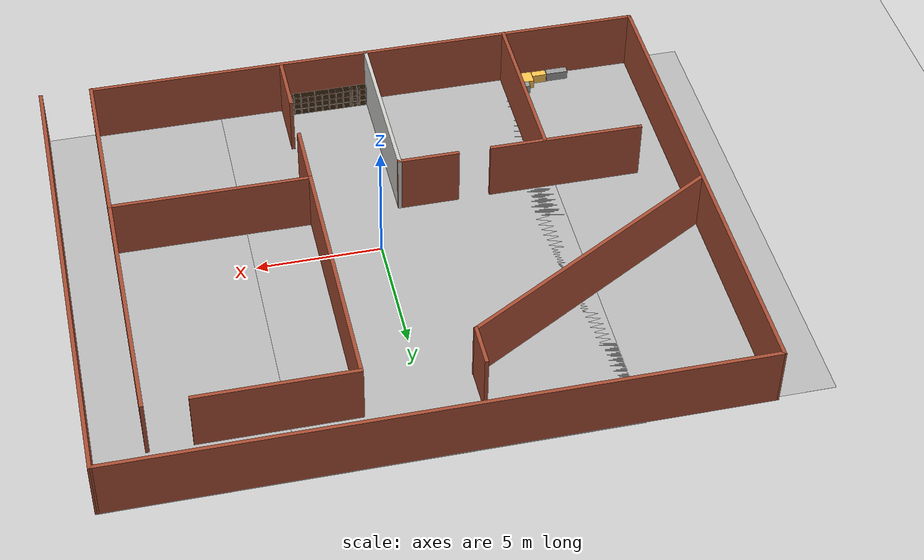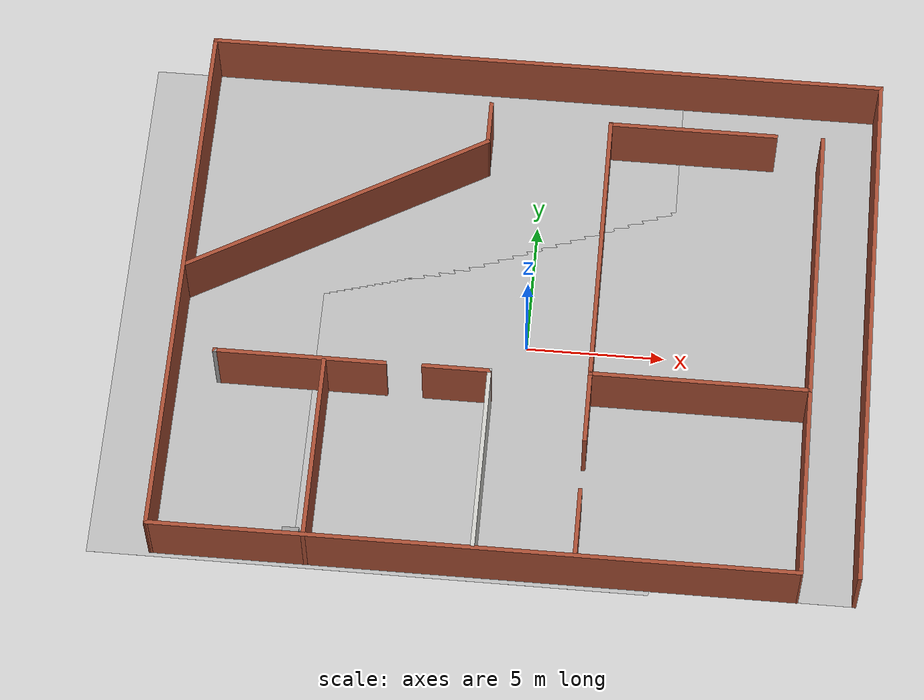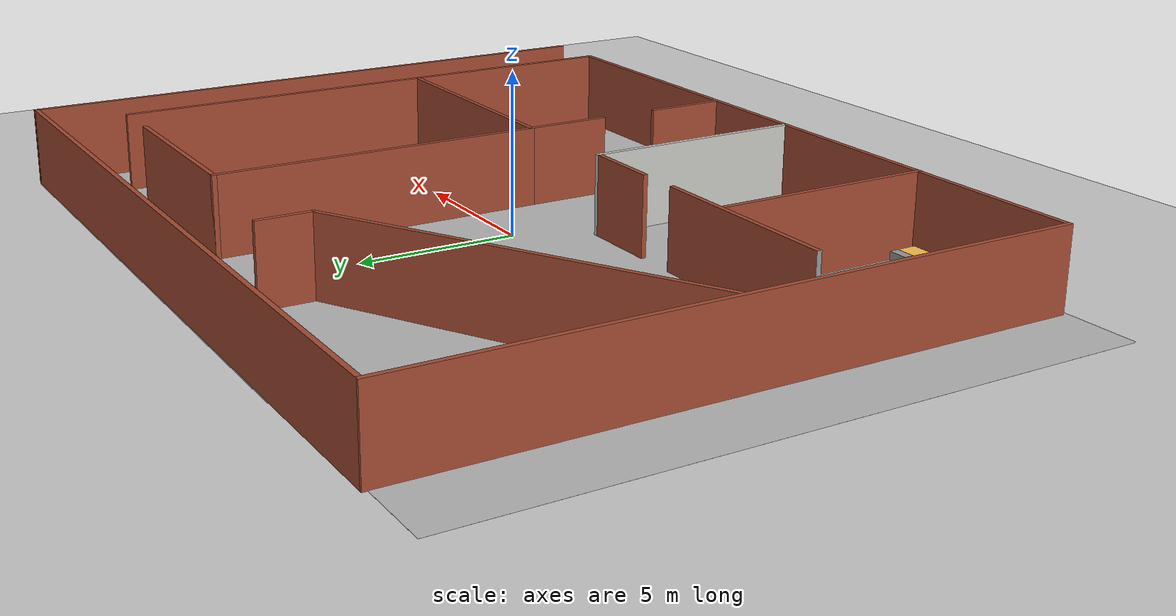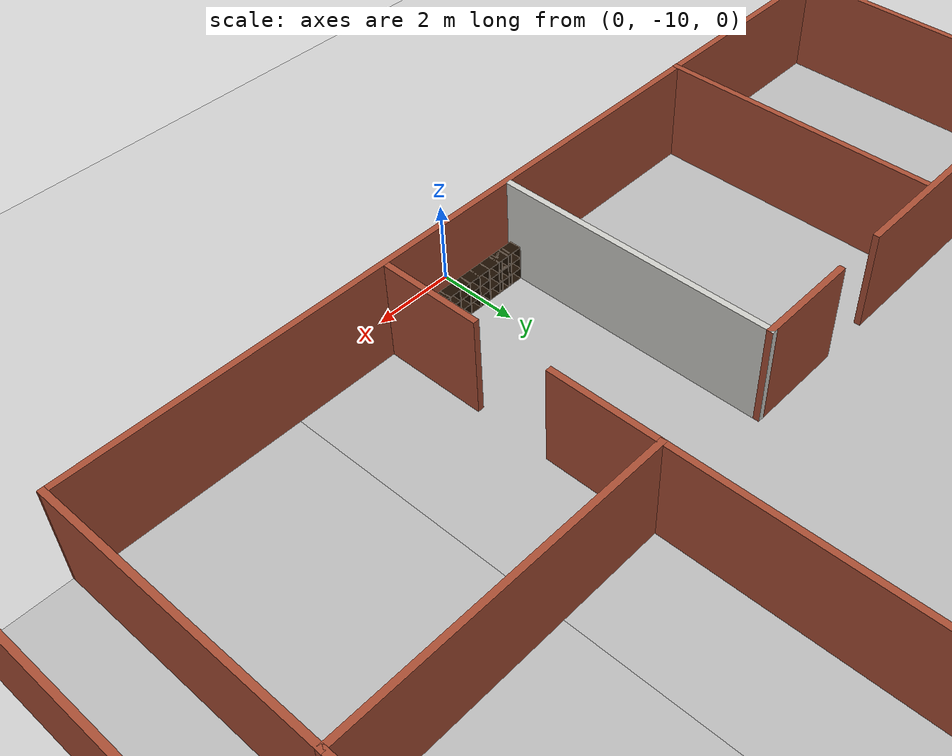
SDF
<sdf version="1.6">
 <world name="default">
  <light name="sun" type="directional">
   <pose>0 0 10 0 -0 0</pose>
   <diffuse>0.8 0.8 0.8 1</diffuse>
   <specular>0.2 0.2 0.2 1</specular>
   <attenuation>
    <range>1000</range>
    <constant>0.9</constant>
    <linear>0.01</linear>
    <quadratic>0.001</quadratic>
   </attenuation>
   <direction>-0.5 0.1 -0.9</direction>
  </light>
  <model name="ground_plane">
   <static>1</static>
   <link name="link">
    <collision name="collision">
     <geometry><plane><normal>0 0 1</normal><size>100 100</size></plane></geometry>
     <surface><friction><ode><mu>100</mu><mu2>50</mu2></ode></friction></surface>
    </collision>
    <visual name="visual">
     <cast_shadows>0</cast_shadows>
     <geometry><plane><normal>0 0 1</normal><size>100 100</size></plane></geometry>
     <material>
      <script><uri>file://media/materials/scripts/gazebo.material</uri><name>Gazebo/Grey</name></script>
     </material>
    </visual>
   </link>
  </model>
  <gravity>0 0 -9.8</gravity>
  <magnetic_field>6e-06 2.3e-05 -4.2e-05</magnetic_field>
  <atmosphere type="adiabatic"/>
  <physics name="default_physics" default="0" type="ode">
   <max_step_size>0.001</max_step_size>
   <real_time_factor>1</real_time_factor>
   <real_time_update_rate>1000</real_time_update_rate>
  </physics>
  <scene><ambient>0.4 0.4 0.4 1</ambient><background>0.7 0.7 0.7 1</background><shadows>1</shadows></scene>
  <audio><device>default</device></audio>
  <spherical_coordinates>
   <surface_model>EARTH_WGS84</surface_model>
   <latitude_deg>0</latitude_deg>
   <longitude_deg>0</longitude_deg>
   <elevation>0</elevation>
   <heading_deg>0</heading_deg>
  </spherical_coordinates>
  <model name="assignment_world">
   <pose>-0.160271 0.770481 0 0 -0 0</pose>
   <link name="Wall_11">
    <collision name="Wall_11_Collision">
     <geometry><box><size>7.25 0.15 2.5</size></box></geometry>
     <pose>0 0 1.25 0 -0 0</pose>
    </collision>
    <visual name="Wall_11_Visual">
     <pose>0 0 1.25 0 -0 0</pose>
     <geometry><box><size>7.25 0.15 2.5</size></box></geometry>
     <material>
      <script><uri>file://media/materials/scripts/gazebo.material</uri><name>Gazebo/Bricks</name></script>
      <ambient>1 1 1 1</ambient>
     </material>
     <meta><layer>0</layer></meta>
    </visual>
    <pose>10.422 -6.36383 0 0 -0 1.5708</pose>
   </link>
   <link name="Wall_12">
    <collision name="Wall_12_Collision">
     <geometry><box><size>8 0.15 2.5</size></box></geometry>
     <pose>0 0 1.25 0 -0 0</pose>
    </collision>
    <visual name="Wall_12_Visual">
     <pose>0 0 1.25 0 -0 0</pose>
     <geometry><box><size>8 0.15 2.5</size></box></geometry>
     <material>
      <script><uri>file://media/materials/scripts/gazebo.material</uri><name>Gazebo/Bricks</name></script>
      <ambient>1 1 1 1</ambient>
     </material>
     <meta><layer>0</layer></meta>
    </visual>
    <pose>6.49702 -2.81383 0 0 -0 3.14159</pose>
   </link>
   <link name="Wall_13">
    <collision name="Wall_13_Collision">
     <geometry><box><size>2.75 0.15 2.5</size></box></geometry>
     <pose>0 0 1.25 0 -0 0</pose>
    </collision>
    <visual name="Wall_13_Visual">
     <pose>0 0 1.25 0 -0 0</pose>
     <geometry><box><size>2.75 0.15 2.5</size></box></geometry>
     <material>
      <script><uri>file://media/materials/scripts/gazebo.material</uri><name>Gazebo/Bricks</name></script>
      <ambient>1 1 1 1</ambient>
     </material>
     <meta><layer>0</layer></meta>
    </visual>
    <pose>2.57202 -4.11383 0 0 -0 -1.5708</pose>
   </link>
   <link name="Wall_15">
    <collision name="Wall_15_Collision">
     <geometry><box><size>2.5 0.15 2.5</size></box></geometry>
     <pose>0 0 1.25 0 -0 0</pose>
    </collision>
    <visual name="Wall_15_Visual">
     <pose>0 0 1.25 0 -0 0</pose>
     <geometry><box><size>2.5 0.15 2.5</size></box></geometry>
     <material>
      <script><uri>file://media/materials/scripts/gazebo.material</uri><name>Gazebo/Bricks</name></script>
      <ambient>1 1 1 1</ambient>
     </material>
     <meta><layer>0</layer></meta>
    </visual>
    <pose>2.56055 -8.598 0 0 -0 -1.5708</pose>
   </link>
   <link name="Wall_17">
    <collision name="Wall_17_Collision">
     <geometry><box><size>10.5 0.15 2.5</size></box></geometry>
     <pose>0 0 1.25 0 -0 0</pose>
    </collision>
    <visual name="Wall_17_Visual">
     <pose>0 0 1.25 0 -0 0</pose>
     <geometry><box><size>10.5 0.15 2.5</size></box></geometry>
     <material>
      <script><uri>file://media/materials/scripts/gazebo.material</uri><name>Gazebo/Bricks</name></script>
      <ambient>1 1 1 1</ambient>
     </material>
     <meta><layer>0</layer></meta>
    </visual>
    <pose>10.422 2.36117 0 0 -0 1.5708</pose>
   </link>
   <link name="Wall_2">
    <collision name="Wall_2_Collision">
     <geometry><box><size>20.0001 0.15 2.5</size></box></geometry>
     <pose>0 0 1.25 0 -0 0</pose>
    </collision>
    <visual name="Wall_2_Visual">
     <pose>0 0 1.25 0 -0 0</pose>
     <geometry><box><size>20.0001 0.15 2.5</size></box></geometry>
     <material>
      <script><uri>file://media/materials/scripts/gazebo.material</uri><name>Gazebo/Bricks</name></script>
      <ambient>1 1 1 1</ambient>
     </material>
     <meta><layer>0</layer></meta>
    </visual>
    <pose>-12.4452 -0.009056 0 0 -0 -1.57314</pose>
   </link>
   <link name="Wall_24">
    <collision name="Wall_24_Collision">
     <geometry><box><size>10.5 0.15 2.5</size></box></geometry>
     <pose>0 0 1.25 0 -0 0</pose>
    </collision>
    <visual name="Wall_24_Visual">
     <pose>0 0 1.25 0 -0 0</pose>
     <geometry><box><size>10.5 0.15 2.5</size></box></geometry>
     <material>
      <script><uri>file://media/materials/scripts/gazebo.material</uri><name>Gazebo/Bricks</name></script>
      <ambient>1 1 1 1</ambient>
     </material>
     <meta><layer>0</layer></meta>
    </visual>
    <pose>2.57202 2.36117 0 0 -0 -1.5708</pose>
   </link>
   <link name="Wall_26">
    <collision name="Wall_26_Collision">
     <geometry><box><size>6.25 0.15 2.5</size></box></geometry>
     <pose>0 0 1.25 0 -0 0</pose>
    </collision>
    <visual name="Wall_26_Visual">
     <pose>0 0 1.25 0 -0 0</pose>
     <geometry><box><size>6.25 0.15 2.5</size></box></geometry>
     <material>
      <script><uri>file://media/materials/scripts/gazebo.material</uri><name>Gazebo/Bricks</name></script>
      <ambient>1 1 1 1</ambient>
     </material>
     <meta><layer>0</layer></meta>
    </visual>
    <pose>5.62202 7.53617 0 0 -0 0</pose>
   </link>
   <link name="Wall_33">
    <collision name="Wall_33_Collision">
     <geometry><box><size>12.25 0.15 2.5</size></box></geometry>
     <pose>0 0 1.25 0 -0 0</pose>
    </collision>
    <visual name="Wall_33_Visual">
     <pose>0 0 1.25 0 -0 0</pose>
     <geometry><box><size>12.25 0.15 2.5</size></box></geometry>
     <material>
      <script><uri>file://media/materials/scripts/gazebo.material</uri><name>Gazebo/Bricks</name></script>
      <ambient>1 1 1 1</ambient>
     </material>
     <meta><layer>0</layer></meta>
    </visual>
    <pose>-7.13474 3.38922 0 0 -0 0.523599</pose>
   </link>
   <link name="Wall_34">
    <collision name="Wall_34_Collision">
     <geometry><box><size>1.75 0.15 2.5</size></box></geometry>
     <pose>0 0 1.25 0 -0 0</pose>
    </collision>
    <visual name="Wall_34_Visual">
     <pose>0 0 1.25 0 -0 0</pose>
     <geometry><box><size>1.75 0.15 2.5</size></box></geometry>
     <material>
      <script><uri>file://media/materials/scripts/gazebo.material</uri><name>Gazebo/Bricks</name></script>
      <ambient>1 1 1 1</ambient>
     </material>
     <meta><layer>0</layer></meta>
    </visual>
    <pose>-1.89529 7.21422 0 0 -0 1.5708</pose>
   </link>
   <link name="Wall_4">
    <collision name="Wall_4_Collision">
     <geometry><box><size>25.0202 0.15 2.5</size></box></geometry>
     <pose>0 0 1.25 0 -0 0</pose>
    </collision>
    <visual name="Wall_4_Visual">
     <pose>0 0 1.25 0 -0 0</pose>
     <geometry><box><size>25.0202 0.15 2.5</size></box></geometry>
     <material>
      <script><uri>file://media/materials/scripts/gazebo.material</uri><name>Gazebo/Bricks</name></script>
      <ambient>1 1 1 1</ambient>
     </material>
     <meta><layer>0</layer></meta>
    </visual>
    <pose>0.033433 9.92606 0 0 -0 0.000813</pose>
   </link>
   <link name="Wall_42">
    <collision name="Wall_42_Collision">
     <geometry><box><size>7 0.15 2.5</size></box></geometry>
     <pose>0 0 1.25 0 -0 0</pose>
    </collision>
    <visual name="Wall_42_Visual">
     <pose>0 0 1.25 0 -0 0</pose>
     <geometry><box><size>7 0.15 2.5</size></box></geometry>
     <material>
      <script><uri>file://media/materials/scripts/gazebo.material</uri><name>Gazebo/CeilingTiled</name></script>
      <ambient>1 1 1 1</ambient>
     </material>
     <meta><layer>0</layer></meta>
    </visual>
    <pose>-1.02106 -6.43398 0 0 -0 1.5708</pose>
   </link>
   <link name="Wall_43">
    <collision name="Wall_43_Collision">
     <geometry><box><size>2.5 0.15 2.5</size></box></geometry>
     <pose>0 0 1.25 0 -0 0</pose>
    </collision>
    <visual name="Wall_43_Visual">
     <pose>0 0 1.25 0 -0 0</pose>
     <geometry><box><size>2.5 0.15 2.5</size></box></geometry>
     <material>
      <script><uri>file://media/materials/scripts/gazebo.material</uri><name>Gazebo/Bricks</name></script>
      <ambient>1 1 1 1</ambient>
     </material>
     <meta><layer>0</layer></meta>
    </visual>
    <pose>-2.19606 -3.00899 0 0 -0 3.14159</pose>
   </link>
   <link name="Wall_45">
    <collision name="Wall_45_Collision">
     <geometry><box><size>7 0.15 2.5</size></box></geometry>
     <pose>0 0 1.25 0 -0 0</pose>
    </collision>
    <visual name="Wall_45_Visual">
     <pose>0 0 1.25 0 -0 0</pose>
     <geometry><box><size>7 0.15 2.5</size></box></geometry>
     <material>
      <script><uri>file://media/materials/scripts/gazebo.material</uri><name>Gazebo/Bricks</name></script>
      <ambient>1 1 1 1</ambient>
     </material>
     <meta><layer>0</layer></meta>
    </visual>
    <pose>-6.94735 -6.51123 0 0 -0 1.5708</pose>
   </link>
   <link name="Wall_47">
    <collision name="Wall_47_Collision">
     <geometry><box><size>6.25 0.15 2.5</size></box></geometry>
     <pose>0 0 1.25 0 -0 0</pose>
    </collision>
    <visual name="Wall_47_Visual">
     <pose>0 0 1.25 0 -0 0</pose>
     <geometry><box><size>6.25 0.15 2.5</size></box></geometry>
     <material>
      <script><uri>file://media/materials/scripts/gazebo.material</uri><name>Gazebo/Bricks</name></script>
      <ambient>1 1 1 1</ambient>
     </material>
     <meta><layer>0</layer></meta>
    </visual>
    <pose>-7.83368 -3.02257 0 0 -0 3.14159</pose>
   </link>
   <link name="Wall_48">
    <collision name="Wall_48_Collision">
     <geometry><box><size>0.15 0.15 2.5</size></box></geometry>
     <pose>0 0 1.25 0 -0 0</pose>
    </collision>
    <visual name="Wall_48_Visual">
     <pose>0 0 1.25 0 -0 0</pose>
     <geometry><box><size>0.15 0.15 2.5</size></box></geometry>
     <material>
      <script><uri>file://media/materials/scripts/gazebo.material</uri><name>Gazebo/Grey</name></script>
      <ambient>1 1 1 1</ambient>
     </material>
     <meta><layer>0</layer></meta>
    </visual>
    <pose>-10.8837 -3.02257 0 0 -0 0</pose>
   </link>
   <link name="Wall_6">
    <collision name="Wall_6_Collision">
     <geometry><box><size>20 0.15 2.5</size></box></geometry>
     <pose>0 0 1.25 0 -0 0</pose>
    </collision>
    <visual name="Wall_6_Visual">
     <pose>0 0 1.25 0 -0 0</pose>
     <geometry><box><size>20 0.15 2.5</size></box></geometry>
     <material>
      <script><uri>file://media/materials/scripts/gazebo.material</uri><name>Gazebo/Bricks</name></script>
      <ambient>1 1 1 1</ambient>
     </material>
     <meta><layer>0</layer></meta>
    </visual>
    <pose>12.4685 0.011172 0 0 -0 -1.5708</pose>
   </link>
   <link name="Wall_8">
    <collision name="Wall_8_Collision">
     <geometry><box><size>23.0202 0.15 2.5</size></box></geometry>
     <pose>0 0 1.25 0 -0 0</pose>
    </collision>
    <visual name="Wall_8_Visual">
     <pose>0 0 1.25 0 -0 0</pose>
     <geometry><box><size>23.0202 0.15 2.5</size></box></geometry>
     <material>
      <script><uri>file://media/materials/scripts/gazebo.material</uri><name>Gazebo/Bricks</name></script>
      <ambient>1 1 1 1</ambient>
     </material>
     <meta><layer>0</layer></meta>
    </visual>
    <pose>-1.01309 -9.92394 0 0 -0 0.000884</pose>
   </link>
   <static>1</static>
  </model>
  <model name="Floor_room">
   <link name="main">
    <pose>0 0 0.01 0 -0 0</pose>
    <collision name="main_Collision"><geometry><box><size>20 20 0.001</size></box></geometry></collision>
    <visual name="main_Visual">
     <geometry><box><size>20 20 0.001</size></box></geometry>
     <material>
      <script>
       <uri>model://Floor_room/materials/scripts</uri>
       <uri>model://Floor_room/materials/textures</uri>
       <name>floor_room</name>
      </script>
     </material>
    </visual>
   </link>
   <static>1</static>
   <pose>-4.93717 0.622613 -0 0 -0 0</pose>
  </model>
  <model name="Floor_room_0">
   <link name="main">
    <pose>0 0 0.01 0 -0 0</pose>
    <collision name="main_Collision"><geometry><box><size>20 20 0.001</size></box></geometry></collision>
    <visual name="main_Visual">
     <geometry><box><size>20 20 0.001</size></box></geometry>
     <material>
      <script>
       <uri>model://Floor_room/materials/scripts</uri>
       <uri>model://Floor_room/materials/textures</uri>
       <name>floor_room</name>
      </script>
     </material>
    </visual>
   </link>
   <static>1</static>
   <pose>2.36558 0.79435 0 0 -0 0</pose>
  </model>
  <model name="Box_33x15">
   <link name="Wall">
    <pose>0 0 0.1985 0 -0 0</pose>
    <inertial>
     <mass>5</mass>
     <inertia><ixx>0.2157</ixx><iyy>0.3597</iyy><izz>0.444</izz><ixy>0</ixy><ixz>0</ixz><iyz>0</iyz></inertia>
    </inertial>
    <collision name="Wall_Collision"><geometry><box><size>0.84 0.6 0.397</size></box></geometry></collision>
    <visual name="Wall_Visual">
     <geometry><box><size>0.84 0.6 0.397</size></box></geometry>
     <material>
      <script><uri>file://media/materials/scripts/gazebo.material</uri><name>Gazebo/Grey</name></script>
      <ambient>1 0.764706 0.305882 1</ambient>
     </material>
    </visual>
   </link>
   <static>1</static>
   <pose>-7.88542 -8.59674 0 0 -0 0</pose>
  </model>
  <model name="Box_24x15W">
   <link name="Wall">
    <pose>0 0 0.1985 0 -0 0</pose>
    <inertial>
     <mass>5</mass>
     <inertia><ixx>0.1022</ixx><iyy>0.2197</iyy><izz>0.1905</izz><ixy>0</ixy><ixz>0</ixz><iyz>0</iyz></inertia>
    </inertial>
    <collision name="Wall_Collision"><geometry><box><size>0.608 0.296 0.397</size></box></geometry></collision>
    <visual name="Wall_Visual">
     <geometry><box><size>0.608 0.296 0.397</size></box></geometry>
     <material>
      <script><uri>file://media/materials/scripts/gazebo.material</uri><name>Gazebo/Grey</name></script>
      <ambient>1 1 1 1</ambient>
     </material>
    </visual>
   </link>
   <static>1</static>
   <pose>-7.76361 -8.14132 0 0 -0 0</pose>
  </model>
  <model name="Box_24x15M">
   <link name="Wall">
    <pose>0 0 0.1985 0 -0 0</pose>
    <inertial>
     <mass>5</mass>
     <inertia><ixx>0.1022</ixx><iyy>0.2197</iyy><izz>0.1905</izz><ixy>0</ixy><ixz>0</ixz><iyz>0</iyz></inertia>
    </inertial>
    <collision name="Wall_Collision"><geometry><box><size>0.608 0.296 0.397</size></box></geometry></collision>
    <visual name="Wall_Visual">
     <geometry><box><size>0.608 0.296 0.397</size></box></geometry>
     <material>
      <script><uri>file://media/materials/scripts/gazebo.material</uri><name>Gazebo/Grey</name></script>
      <ambient>1 0.764706 0.305882 1</ambient>
     </material>
    </visual>
   </link>
   <static>1</static>
   <pose>-8.62222 -8.73787 0 0 -0 0</pose>
  </model>
  <model name="Box_36x15W">
   <link name="Wall">
    <pose>0 0 0.1985 0 -0 0</pose>
    <inertial>
     <mass>5</mass>
     <inertia><ixx>0.1022</ixx><iyy>0.4107</iyy><izz>0.3815</izz><ixy>0</ixy><ixz>0</ixz><iyz>0</iyz></inertia>
    </inertial>
    <collision name="Wall_Collision"><geometry><box><size>0.91 0.296 0.397</size></box></geometry></collision>
    <visual name="Wall_Visual">
     <geometry><box><size>0.91 0.296 0.397</size></box></geometry>
     <material>
      <script><uri>file://media/materials/scripts/gazebo.material</uri><name>Gazebo/Grey</name></script>
      <ambient>1 1 1 1</ambient>
     </material>
    </visual>
   </link>
   <static>1</static>
   <pose>-9.40603 -8.75664 0 0 -0 0</pose>
  </model>
  <model name="6_Cube_StorageE">
   <link name="Wall_0">
    <pose>0 0 0.01 0 -0 0</pose>
    <inertial>
     <mass>1.6201</mass>
     <inertia><ixx>0.0119</ixx><iyy>0.0631</iyy><izz>0.0513</izz><ixy>0</ixy><ixz>0</ixz><iyz>0</iyz></inertia>
    </inertial>
    <collision name="Wall_0_Collision"><geometry><box><size>0.616 0.296 0.02</size></box></geometry></collision>
    <visual name="Wall_0_Visual">
     <geometry><box><size>0.616 0.296 0.02</size></box></geometry>
     <material>
      <script><uri>file://media/materials/scripts/gazebo.material</uri><name>Gazebo/Grey</name></script>
      <ambient>0.105882 0.0509804 0 1</ambient>
     </material>
    </visual>
   </link>
   <joint name="0_2" type="fixed">
    <pose>-0.308 0 0 0 -0 0</pose>
    <parent>Wall_2</parent>
    <child>Wall_0</child>
    <axis>
     <xyz>1 0 0</xyz>
     <use_parent_model_frame>0</use_parent_model_frame>
     <limit><lower>-1e+16</lower><upper>1e+16</upper></limit>
    </axis>
   </joint>
   <joint name="0_12" type="fixed">
    <parent>Wall_12</parent>
    <child>Wall_0</child>
    <axis>
     <xyz>0 0 1</xyz>
     <use_parent_model_frame>0</use_parent_model_frame>
     <limit><lower>-1e+16</lower><upper>1e+16</upper></limit>
    </axis>
   </joint>
   <joint name="0_4" type="fixed">
    <pose>0.308 0 0 0 -0 0</pose>
    <parent>Wall_4</parent>
    <child>Wall_0</child>
    <axis>
     <xyz>1 0 0</xyz>
     <use_parent_model_frame>0</use_parent_model_frame>
     <limit><lower>-1e+16</lower><upper>1e+16</upper></limit>
    </axis>
   </joint>
   <link name="Wall_10">
    <pose>0 0 0.61 0 -0 0</pose>
    <inertial>
     <mass>1.6201</mass>
     <inertia><ixx>0.0119</ixx><iyy>0.0631</iyy><izz>0.0513</izz><ixy>0</ixy><ixz>0</ixz><iyz>0</iyz></inertia>
    </inertial>
    <collision name="Wall_10_Collision"><geometry><box><size>0.616 0.296 0.02</size></box></geometry></collision>
    <visual name="Wall_10_Visual">
     <geometry><box><size>0.616 0.296 0.02</size></box></geometry>
     <material>
      <script><uri>file://media/materials/scripts/gazebo.material</uri><name>Gazebo/Grey</name></script>
      <ambient>0.105882 0.0509804 0 1</ambient>
     </material>
    </visual>
   </link>
   <joint name="10_2" type="fixed">
    <pose>-0.308 0 0 0 -0 0</pose>
    <parent>Wall_2</parent>
    <child>Wall_10</child>
    <axis>
     <xyz>1 0 0</xyz>
     <use_parent_model_frame>0</use_parent_model_frame>
     <limit><lower>-1e+16</lower><upper>1e+16</upper></limit>
    </axis>
   </joint>
   <joint name="10_12" type="fixed">
    <parent>Wall_12</parent>
    <child>Wall_10</child>
    <axis>
     <xyz>0 0 1</xyz>
     <use_parent_model_frame>0</use_parent_model_frame>
     <limit><lower>-1e+16</lower><upper>1e+16</upper></limit>
    </axis>
   </joint>
   <joint name="10_4" type="fixed">
    <pose>0.308 0 0 0 -0 0</pose>
    <parent>Wall_4</parent>
    <child>Wall_10</child>
    <axis>
     <xyz>1 0 0</xyz>
     <use_parent_model_frame>0</use_parent_model_frame>
     <limit><lower>-1e+16</lower><upper>1e+16</upper></limit>
    </axis>
   </joint>
   <link name="Wall_12">
    <pose>0 0 0.4575 0 -0 0</pose>
    <inertial>
     <mass>2.4065</mass>
     <inertia><ixx>0.0177</ixx><iyy>0.1855</iyy><izz>0.168</izz><ixy>0</ixy><ixz>0</ixz><iyz>0</iyz></inertia>
    </inertial>
    <collision name="Wall_12_Collision"><geometry><box><size>0.02 0.296 0.915</size></box></geometry></collision>
    <visual name="Wall_12_Visual">
     <geometry><box><size>0.02 0.296 0.915</size></box></geometry>
     <material>
      <script><uri>file://media/materials/scripts/gazebo.material</uri><name>Gazebo/Grey</name></script>
      <ambient>0.105882 0.0509804 0 1</ambient>
     </material>
    </visual>
   </link>
   <link name="Wall_2">
    <pose>-0.298 0 0.4575 0 -0 0</pose>
    <inertial>
     <mass>2.4065</mass>
     <inertia><ixx>0.0177</ixx><iyy>0.1855</iyy><izz>0.168</izz><ixy>0</ixy><ixz>0</ixz><iyz>0</iyz></inertia>
    </inertial>
    <collision name="Wall_2_Collision"><geometry><box><size>0.02 0.296 0.915</size></box></geometry></collision>
    <visual name="Wall_2_Visual">
     <geometry><box><size>0.02 0.296 0.915</size></box></geometry>
     <material>
      <script><uri>file://media/materials/scripts/gazebo.material</uri><name>Gazebo/Grey</name></script>
      <ambient>0.105882 0.0509804 0 1</ambient>
     </material>
    </visual>
   </link>
   <link name="Wall_4">
    <pose>0.298 0 0.4575 0 -0 0</pose>
    <inertial>
     <mass>2.4065</mass>
     <inertia><ixx>0.0177</ixx><iyy>0.1855</iyy><izz>0.168</izz><ixy>0</ixy><ixz>0</ixz><iyz>0</iyz></inertia>
    </inertial>
    <collision name="Wall_4_Collision"><geometry><box><size>0.02 0.296 0.915</size></box></geometry></collision>
    <visual name="Wall_4_Visual">
     <geometry><box><size>0.02 0.296 0.915</size></box></geometry>
     <material>
      <script><uri>file://media/materials/scripts/gazebo.material</uri><name>Gazebo/Grey</name></script>
      <ambient>0.105882 0.0509804 0 1</ambient>
     </material>
    </visual>
   </link>
   <link name="Wall_6">
    <pose>0 0 0.905 0 -0 0</pose>
    <inertial>
     <mass>1.6201</mass>
     <inertia><ixx>0.0119</ixx><iyy>0.0631</iyy><izz>0.0513</izz><ixy>0</ixy><ixz>0</ixz><iyz>0</iyz></inertia>
    </inertial>
    <collision name="Wall_6_Collision"><geometry><box><size>0.616 0.296 0.02</size></box></geometry></collision>
    <visual name="Wall_6_Visual">
     <geometry><box><size>0.616 0.296 0.02</size></box></geometry>
     <material>
      <script><uri>file://media/materials/scripts/gazebo.material</uri><name>Gazebo/Grey</name></script>
      <ambient>0.105882 0.0509804 0 1</ambient>
     </material>
    </visual>
   </link>
   <joint name="6_2" type="fixed">
    <pose>-0.308 0 0 0 -0 0</pose>
    <parent>Wall_2</parent>
    <child>Wall_6</child>
    <axis>
     <xyz>2 0 0</xyz>
     <use_parent_model_frame>0</use_parent_model_frame>
     <limit><lower>-1e+16</lower><upper>1e+16</upper></limit>
    </axis>
   </joint>
   <joint name="6_12" type="fixed">
    <parent>Wall_12</parent>
    <child>Wall_6</child>
    <axis>
     <xyz>0 0 1</xyz>
     <use_parent_model_frame>0</use_parent_model_frame>
     <limit><lower>-1e+16</lower><upper>1e+16</upper></limit>
    </axis>
   </joint>
   <joint name="6_4" type="fixed">
    <pose>0.308 0 0 0 -0 0</pose>
    <parent>Wall_4</parent>
    <child>Wall_6</child>
    <axis>
     <xyz>1 0 0</xyz>
     <use_parent_model_frame>0</use_parent_model_frame>
     <limit><lower>-1e+16</lower><upper>1e+16</upper></limit>
    </axis>
   </joint>
   <link name="Wall_8">
    <pose>0 0 0.305 0 -0 0</pose>
    <inertial>
     <mass>1.6201</mass>
     <inertia><ixx>0.0119</ixx><iyy>0.0631</iyy><izz>0.0513</izz><ixy>0</ixy><ixz>0</ixz><iyz>0</iyz></inertia>
    </inertial>
    <collision name="Wall_8_Collision"><geometry><box><size>0.616 0.296 0.02</size></box></geometry></collision>
    <visual name="Wall_8_Visual">
     <geometry><box><size>0.616 0.296 0.02</size></box></geometry>
     <material>
      <script><uri>file://media/materials/scripts/gazebo.material</uri><name>Gazebo/Grey</name></script>
      <ambient>0.105882 0.0509804 0 1</ambient>
     </material>
    </visual>
   </link>
   <joint name="8_2" type="fixed">
    <pose>-0.308 0 0 0 -0 0</pose>
    <parent>Wall_2</parent>
    <child>Wall_8</child>
    <axis>
     <xyz>1 0 0</xyz>
     <use_parent_model_frame>0</use_parent_model_frame>
     <limit><lower>-1e+16</lower><upper>1e+16</upper></limit>
    </axis>
   </joint>
   <joint name="8_12" type="fixed">
    <parent>Wall_12</parent>
    <child>Wall_8</child>
    <axis>
     <xyz>0 0 1</xyz>
     <use_parent_model_frame>0</use_parent_model_frame>
     <limit><lower>-1e+16</lower><upper>1e+16</upper></limit>
    </axis>
   </joint>
   <joint name="8_4" type="fixed">
    <pose>0.308 0 0 0 -0 0</pose>
    <parent>Wall_4</parent>
    <child>Wall_8</child>
    <axis>
     <xyz>1 0 0</xyz>
     <use_parent_model_frame>0</use_parent_model_frame>
     <limit><lower>-1e+16</lower><upper>1e+16</upper></limit>
    </axis>
   </joint>
   <static>1</static>
   <pose>1.98429 -8.86591 0 0 -0 0</pose>
  </model>
  <model name="6_Cube_StorageE_clone">
   <link name="Wall_0">
    <pose>0 0 0.01 0 -0 0</pose>
    <inertial>
     <mass>1.6201</mass>
     <inertia><ixx>0.0119</ixx><iyy>0.0631</iyy><izz>0.0513</izz><ixy>0</ixy><ixz>0</ixz><iyz>0</iyz></inertia>
    </inertial>
    <collision name="Wall_0_Collision"><geometry><box><size>0.616 0.296 0.02</size></box></geometry></collision>
    <visual name="Wall_0_Visual">
     <geometry><box><size>0.616 0.296 0.02</size></box></geometry>
     <material>
      <script><uri>file://media/materials/scripts/gazebo.material</uri><name>Gazebo/Grey</name></script>
      <ambient>0.105882 0.0509804 0 1</ambient>
     </material>
    </visual>
   </link>
   <joint name="0_2" type="fixed">
    <pose>-0.308 0 0 0 -0 0</pose>
    <parent>Wall_2</parent>
    <child>Wall_0</child>
    <axis>
     <xyz>1 0 0</xyz>
     <use_parent_model_frame>0</use_parent_model_frame>
     <limit><lower>-1e+16</lower><upper>1e+16</upper></limit>
    </axis>
   </joint>
   <joint name="0_12" type="fixed">
    <parent>Wall_12</parent>
    <child>Wall_0</child>
    <axis>
     <xyz>0 0 1</xyz>
     <use_parent_model_frame>0</use_parent_model_frame>
     <limit><lower>-1e+16</lower><upper>1e+16</upper></limit>
    </axis>
   </joint>
   <joint name="0_4" type="fixed">
    <pose>0.308 0 0 0 -0 0</pose>
    <parent>Wall_4</parent>
    <child>Wall_0</child>
    <axis>
     <xyz>1 0 0</xyz>
     <use_parent_model_frame>0</use_parent_model_frame>
     <limit><lower>-1e+16</lower><upper>1e+16</upper></limit>
    </axis>
   </joint>
   <link name="Wall_10">
    <pose>0 0 0.61 0 -0 0</pose>
    <inertial>
     <mass>1.6201</mass>
     <inertia><ixx>0.0119</ixx><iyy>0.0631</iyy><izz>0.0513</izz><ixy>0</ixy><ixz>0</ixz><iyz>0</iyz></inertia>
    </inertial>
    <collision name="Wall_10_Collision"><geometry><box><size>0.616 0.296 0.02</size></box></geometry></collision>
    <visual name="Wall_10_Visual">
     <geometry><box><size>0.616 0.296 0.02</size></box></geometry>
     <material>
      <script><uri>file://media/materials/scripts/gazebo.material</uri><name>Gazebo/Grey</name></script>
      <ambient>0.105882 0.0509804 0 1</ambient>
     </material>
    </visual>
   </link>
   <joint name="10_2" type="fixed">
    <pose>-0.308 0 0 0 -0 0</pose>
    <parent>Wall_2</parent>
    <child>Wall_10</child>
    <axis>
     <xyz>1 0 0</xyz>
     <use_parent_model_frame>0</use_parent_model_frame>
     <limit><lower>-1e+16</lower><upper>1e+16</upper></limit>
    </axis>
   </joint>
   <joint name="10_12" type="fixed">
    <parent>Wall_12</parent>
    <child>Wall_10</child>
    <axis>
     <xyz>0 0 1</xyz>
     <use_parent_model_frame>0</use_parent_model_frame>
     <limit><lower>-1e+16</lower><upper>1e+16</upper></limit>
    </axis>
   </joint>
   <joint name="10_4" type="fixed">
    <pose>0.308 0 0 0 -0 0</pose>
    <parent>Wall_4</parent>
    <child>Wall_10</child>
    <axis>
     <xyz>1 0 0</xyz>
     <use_parent_model_frame>0</use_parent_model_frame>
     <limit><lower>-1e+16</lower><upper>1e+16</upper></limit>
    </axis>
   </joint>
   <link name="Wall_12">
    <pose>0 0 0.4575 0 -0 0</pose>
    <inertial>
     <mass>2.4065</mass>
     <inertia><ixx>0.0177</ixx><iyy>0.1855</iyy><izz>0.168</izz><ixy>0</ixy><ixz>0</ixz><iyz>0</iyz></inertia>
    </inertial>
    <collision name="Wall_12_Collision"><geometry><box><size>0.02 0.296 0.915</size></box></geometry></collision>
    <visual name="Wall_12_Visual">
     <geometry><box><size>0.02 0.296 0.915</size></box></geometry>
     <material>
      <script><uri>file://media/materials/scripts/gazebo.material</uri><name>Gazebo/Grey</name></script>
      <ambient>0.105882 0.0509804 0 1</ambient>
     </material>
    </visual>
   </link>
   <link name="Wall_2">
    <pose>-0.298 0 0.4575 0 -0 0</pose>
    <inertial>
     <mass>2.4065</mass>
     <inertia><ixx>0.0177</ixx><iyy>0.1855</iyy><izz>0.168</izz><ixy>0</ixy><ixz>0</ixz><iyz>0</iyz></inertia>
    </inertial>
    <collision name="Wall_2_Collision"><geometry><box><size>0.02 0.296 0.915</size></box></geometry></collision>
    <visual name="Wall_2_Visual">
     <geometry><box><size>0.02 0.296 0.915</size></box></geometry>
     <material>
      <script><uri>file://media/materials/scripts/gazebo.material</uri><name>Gazebo/Grey</name></script>
      <ambient>0.105882 0.0509804 0 1</ambient>
     </material>
    </visual>
   </link>
   <link name="Wall_4">
    <pose>0.298 0 0.4575 0 -0 0</pose>
    <inertial>
     <mass>2.4065</mass>
     <inertia><ixx>0.0177</ixx><iyy>0.1855</iyy><izz>0.168</izz><ixy>0</ixy><ixz>0</ixz><iyz>0</iyz></inertia>
    </inertial>
    <collision name="Wall_4_Collision"><geometry><box><size>0.02 0.296 0.915</size></box></geometry></collision>
    <visual name="Wall_4_Visual">
     <geometry><box><size>0.02 0.296 0.915</size></box></geometry>
     <material>
      <script><uri>file://media/materials/scripts/gazebo.material</uri><name>Gazebo/Grey</name></script>
      <ambient>0.105882 0.0509804 0 1</ambient>
     </material>
    </visual>
   </link>
   <link name="Wall_6">
    <pose>0 0 0.905 0 -0 0</pose>
    <inertial>
     <mass>1.6201</mass>
     <inertia><ixx>0.0119</ixx><iyy>0.0631</iyy><izz>0.0513</izz><ixy>0</ixy><ixz>0</ixz><iyz>0</iyz></inertia>
    </inertial>
    <collision name="Wall_6_Collision"><geometry><box><size>0.616 0.296 0.02</size></box></geometry></collision>
    <visual name="Wall_6_Visual">
     <geometry><box><size>0.616 0.296 0.02</size></box></geometry>
     <material>
      <script><uri>file://media/materials/scripts/gazebo.material</uri><name>Gazebo/Grey</name></script>
      <ambient>0.105882 0.0509804 0 1</ambient>
     </material>
    </visual>
   </link>
   <joint name="6_2" type="fixed">
    <pose>-0.308 0 0 0 -0 0</pose>
    <parent>Wall_2</parent>
    <child>Wall_6</child>
    <axis>
     <xyz>2 0 0</xyz>
     <use_parent_model_frame>0</use_parent_model_frame>
     <limit><lower>-1e+16</lower><upper>1e+16</upper></limit>
    </axis>
   </joint>
   <joint name="6_12" type="fixed">
    <parent>Wall_12</parent>
    <child>Wall_6</child>
    <axis>
     <xyz>0 0 1</xyz>
     <use_parent_model_frame>0</use_parent_model_frame>
     <limit><lower>-1e+16</lower><upper>1e+16</upper></limit>
    </axis>
   </joint>
   <joint name="6_4" type="fixed">
    <pose>0.308 0 0 0 -0 0</pose>
    <parent>Wall_4</parent>
    <child>Wall_6</child>
    <axis>
     <xyz>1 0 0</xyz>
     <use_parent_model_frame>0</use_parent_model_frame>
     <limit><lower>-1e+16</lower><upper>1e+16</upper></limit>
    </axis>
   </joint>
   <link name="Wall_8">
    <pose>0 0 0.305 0 -0 0</pose>
    <inertial>
     <mass>1.6201</mass>
     <inertia><ixx>0.0119</ixx><iyy>0.0631</iyy><izz>0.0513</izz><ixy>0</ixy><ixz>0</ixz><iyz>0</iyz></inertia>
    </inertial>
    <collision name="Wall_8_Collision"><geometry><box><size>0.616 0.296 0.02</size></box></geometry></collision>
    <visual name="Wall_8_Visual">
     <geometry><box><size>0.616 0.296 0.02</size></box></geometry>
     <material>
      <script><uri>file://media/materials/scripts/gazebo.material</uri><name>Gazebo/Grey</name></script>
      <ambient>0.105882 0.0509804 0 1</ambient>
     </material>
    </visual>
   </link>
   <joint name="8_2" type="fixed">
    <pose>-0.308 0 0 0 -0 0</pose>
    <parent>Wall_2</parent>
    <child>Wall_8</child>
    <axis>
     <xyz>1 0 0</xyz>
     <use_parent_model_frame>0</use_parent_model_frame>
     <limit><lower>-1e+16</lower><upper>1e+16</upper></limit>
    </axis>
   </joint>
   <joint name="8_12" type="fixed">
    <parent>Wall_12</parent>
    <child>Wall_8</child>
    <axis>
     <xyz>0 0 1</xyz>
     <use_parent_model_frame>0</use_parent_model_frame>
     <limit><lower>-1e+16</lower><upper>1e+16</upper></limit>
    </axis>
   </joint>
   <joint name="8_4" type="fixed">
    <pose>0.308 0 0 0 -0 0</pose>
    <parent>Wall_4</parent>
    <child>Wall_8</child>
    <axis>
     <xyz>1 0 0</xyz>
     <use_parent_model_frame>0</use_parent_model_frame>
     <limit><lower>-1e+16</lower><upper>1e+16</upper></limit>
    </axis>
   </joint>
   <static>1</static>
   <pose>1.38135 -8.86183 0 0 -0 0</pose>
  </model>
  <model name="6_Cube_StorageE_clone_0">
   <link name="Wall_0">
    <pose>0 0 0.01 0 -0 0</pose>
    <inertial>
     <mass>1.6201</mass>
     <inertia><ixx>0.0119</ixx><iyy>0.0631</iyy><izz>0.0513</izz><ixy>0</ixy><ixz>0</ixz><iyz>0</iyz></inertia>
    </inertial>
    <collision name="Wall_0_Collision"><geometry><box><size>0.616 0.296 0.02</size></box></geometry></collision>
    <visual name="Wall_0_Visual">
     <geometry><box><size>0.616 0.296 0.02</size></box></geometry>
     <material>
      <script><uri>file://media/materials/scripts/gazebo.material</uri><name>Gazebo/Grey</name></script>
      <ambient>0.105882 0.0509804 0 1</ambient>
     </material>
    </visual>
   </link>
   <joint name="0_2" type="fixed">
    <pose>-0.308 0 0 0 -0 0</pose>
    <parent>Wall_2</parent>
    <child>Wall_0</child>
    <axis>
     <xyz>1 0 0</xyz>
     <use_parent_model_frame>0</use_parent_model_frame>
     <limit><lower>-1e+16</lower><upper>1e+16</upper></limit>
    </axis>
   </joint>
   <joint name="0_12" type="fixed">
    <parent>Wall_12</parent>
    <child>Wall_0</child>
    <axis>
     <xyz>0 0 1</xyz>
     <use_parent_model_frame>0</use_parent_model_frame>
     <limit><lower>-1e+16</lower><upper>1e+16</upper></limit>
    </axis>
   </joint>
   <joint name="0_4" type="fixed">
    <pose>0.308 0 0 0 -0 0</pose>
    <parent>Wall_4</parent>
    <child>Wall_0</child>
    <axis>
     <xyz>1 0 0</xyz>
     <use_parent_model_frame>0</use_parent_model_frame>
     <limit><lower>-1e+16</lower><upper>1e+16</upper></limit>
    </axis>
   </joint>
   <link name="Wall_10">
    <pose>0 0 0.61 0 -0 0</pose>
    <inertial>
     <mass>1.6201</mass>
     <inertia><ixx>0.0119</ixx><iyy>0.0631</iyy><izz>0.0513</izz><ixy>0</ixy><ixz>0</ixz><iyz>0</iyz></inertia>
    </inertial>
    <collision name="Wall_10_Collision"><geometry><box><size>0.616 0.296 0.02</size></box></geometry></collision>
    <visual name="Wall_10_Visual">
     <geometry><box><size>0.616 0.296 0.02</size></box></geometry>
     <material>
      <script><uri>file://media/materials/scripts/gazebo.material</uri><name>Gazebo/Grey</name></script>
      <ambient>0.105882 0.0509804 0 1</ambient>
     </material>
    </visual>
   </link>
   <joint name="10_2" type="fixed">
    <pose>-0.308 0 0 0 -0 0</pose>
    <parent>Wall_2</parent>
    <child>Wall_10</child>
    <axis>
     <xyz>1 0 0</xyz>
     <use_parent_model_frame>0</use_parent_model_frame>
     <limit><lower>-1e+16</lower><upper>1e+16</upper></limit>
    </axis>
   </joint>
   <joint name="10_12" type="fixed">
    <parent>Wall_12</parent>
    <child>Wall_10</child>
    <axis>
     <xyz>0 0 1</xyz>
     <use_parent_model_frame>0</use_parent_model_frame>
     <limit><lower>-1e+16</lower><upper>1e+16</upper></limit>
    </axis>
   </joint>
   <joint name="10_4" type="fixed">
    <pose>0.308 0 0 0 -0 0</pose>
    <parent>Wall_4</parent>
    <child>Wall_10</child>
    <axis>
     <xyz>1 0 0</xyz>
     <use_parent_model_frame>0</use_parent_model_frame>
     <limit><lower>-1e+16</lower><upper>1e+16</upper></limit>
    </axis>
   </joint>
   <link name="Wall_12">
    <pose>0 0 0.4575 0 -0 0</pose>
    <inertial>
     <mass>2.4065</mass>
     <inertia><ixx>0.0177</ixx><iyy>0.1855</iyy><izz>0.168</izz><ixy>0</ixy><ixz>0</ixz><iyz>0</iyz></inertia>
    </inertial>
    <collision name="Wall_12_Collision"><geometry><box><size>0.02 0.296 0.915</size></box></geometry></collision>
    <visual name="Wall_12_Visual">
     <geometry><box><size>0.02 0.296 0.915</size></box></geometry>
     <material>
      <script><uri>file://media/materials/scripts/gazebo.material</uri><name>Gazebo/Grey</name></script>
      <ambient>0.105882 0.0509804 0 1</ambient>
     </material>
    </visual>
   </link>
   <link name="Wall_2">
    <pose>-0.298 0 0.4575 0 -0 0</pose>
    <inertial>
     <mass>2.4065</mass>
     <inertia><ixx>0.0177</ixx><iyy>0.1855</iyy><izz>0.168</izz><ixy>0</ixy><ixz>0</ixz><iyz>0</iyz></inertia>
    </inertial>
    <collision name="Wall_2_Collision"><geometry><box><size>0.02 0.296 0.915</size></box></geometry></collision>
    <visual name="Wall_2_Visual">
     <geometry><box><size>0.02 0.296 0.915</size></box></geometry>
     <material>
      <script><uri>file://media/materials/scripts/gazebo.material</uri><name>Gazebo/Grey</name></script>
      <ambient>0.105882 0.0509804 0 1</ambient>
     </material>
    </visual>
   </link>
   <link name="Wall_4">
    <pose>0.298 0 0.4575 0 -0 0</pose>
    <inertial>
     <mass>2.4065</mass>
     <inertia><ixx>0.0177</ixx><iyy>0.1855</iyy><izz>0.168</izz><ixy>0</ixy><ixz>0</ixz><iyz>0</iyz></inertia>
    </inertial>
    <collision name="Wall_4_Collision"><geometry><box><size>0.02 0.296 0.915</size></box></geometry></collision>
    <visual name="Wall_4_Visual">
     <geometry><box><size>0.02 0.296 0.915</size></box></geometry>
     <material>
      <script><uri>file://media/materials/scripts/gazebo.material</uri><name>Gazebo/Grey</name></script>
      <ambient>0.105882 0.0509804 0 1</ambient>
     </material>
    </visual>
   </link>
   <link name="Wall_6">
    <pose>0 0 0.905 0 -0 0</pose>
    <inertial>
     <mass>1.6201</mass>
     <inertia><ixx>0.0119</ixx><iyy>0.0631</iyy><izz>0.0513</izz><ixy>0</ixy><ixz>0</ixz><iyz>0</iyz></inertia>
    </inertial>
    <collision name="Wall_6_Collision"><geometry><box><size>0.616 0.296 0.02</size></box></geometry></collision>
    <visual name="Wall_6_Visual">
     <geometry><box><size>0.616 0.296 0.02</size></box></geometry>
     <material>
      <script><uri>file://media/materials/scripts/gazebo.material</uri><name>Gazebo/Grey</name></script>
      <ambient>0.105882 0.0509804 0 1</ambient>
     </material>
    </visual>
   </link>
   <joint name="6_2" type="fixed">
    <pose>-0.308 0 0 0 -0 0</pose>
    <parent>Wall_2</parent>
    <child>Wall_6</child>
    <axis>
     <xyz>2 0 0</xyz>
     <use_parent_model_frame>0</use_parent_model_frame>
     <limit><lower>-1e+16</lower><upper>1e+16</upper></limit>
    </axis>
   </joint>
   <joint name="6_12" type="fixed">
    <parent>Wall_12</parent>
    <child>Wall_6</child>
    <axis>
     <xyz>0 0 1</xyz>
     <use_parent_model_frame>0</use_parent_model_frame>
     <limit><lower>-1e+16</lower><upper>1e+16</upper></limit>
    </axis>
   </joint>
   <joint name="6_4" type="fixed">
    <pose>0.308 0 0 0 -0 0</pose>
    <parent>Wall_4</parent>
    <child>Wall_6</child>
    <axis>
     <xyz>1 0 0</xyz>
     <use_parent_model_frame>0</use_parent_model_frame>
     <limit><lower>-1e+16</lower><upper>1e+16</upper></limit>
    </axis>
   </joint>
   <link name="Wall_8">
    <pose>0 0 0.305 0 -0 0</pose>
    <inertial>
     <mass>1.6201</mass>
     <inertia><ixx>0.0119</ixx><iyy>0.0631</iyy><izz>0.0513</izz><ixy>0</ixy><ixz>0</ixz><iyz>0</iyz></inertia>
    </inertial>
    <collision name="Wall_8_Collision"><geometry><box><size>0.616 0.296 0.02</size></box></geometry></collision>
    <visual name="Wall_8_Visual">
     <geometry><box><size>0.616 0.296 0.02</size></box></geometry>
     <material>
      <script><uri>file://media/materials/scripts/gazebo.material</uri><name>Gazebo/Grey</name></script>
      <ambient>0.105882 0.0509804 0 1</ambient>
     </material>
    </visual>
   </link>
   <joint name="8_2" type="fixed">
    <pose>-0.308 0 0 0 -0 0</pose>
    <parent>Wall_2</parent>
    <child>Wall_8</child>
    <axis>
     <xyz>1 0 0</xyz>
     <use_parent_model_frame>0</use_parent_model_frame>
     <limit><lower>-1e+16</lower><upper>1e+16</upper></limit>
    </axis>
   </joint>
   <joint name="8_12" type="fixed">
    <parent>Wall_12</parent>
    <child>Wall_8</child>
    <axis>
     <xyz>0 0 1</xyz>
     <use_parent_model_frame>0</use_parent_model_frame>
     <limit><lower>-1e+16</lower><upper>1e+16</upper></limit>
    </axis>
   </joint>
   <joint name="8_4" type="fixed">
    <pose>0.308 0 0 0 -0 0</pose>
    <parent>Wall_4</parent>
    <child>Wall_8</child>
    <axis>
     <xyz>1 0 0</xyz>
     <use_parent_model_frame>0</use_parent_model_frame>
     <limit><lower>-1e+16</lower><upper>1e+16</upper></limit>
    </axis>
   </joint>
   <static>1</static>
   <pose>0.781318 -8.86225 0 0 -0 0</pose>
  </model>
  <model name="6_Cube_StorageE_clone_1">
   <link name="Wall_0">
    <pose>0 0 0.01 0 -0 0</pose>
    <inertial>
     <mass>1.6201</mass>
     <inertia><ixx>0.0119</ixx><iyy>0.0631</iyy><izz>0.0513</izz><ixy>0</ixy><ixz>0</ixz><iyz>0</iyz></inertia>
    </inertial>
    <collision name="Wall_0_Collision"><geometry><box><size>0.616 0.296 0.02</size></box></geometry></collision>
    <visual name="Wall_0_Visual">
     <geometry><box><size>0.616 0.296 0.02</size></box></geometry>
     <material>
      <script><uri>file://media/materials/scripts/gazebo.material</uri><name>Gazebo/Grey</name></script>
      <ambient>0.105882 0.0509804 0 1</ambient>
     </material>
    </visual>
   </link>
   <joint name="0_2" type="fixed">
    <pose>-0.308 0 0 0 -0 0</pose>
    <parent>Wall_2</parent>
    <child>Wall_0</child>
    <axis>
     <xyz>1 0 0</xyz>
     <use_parent_model_frame>0</use_parent_model_frame>
     <limit><lower>-1e+16</lower><upper>1e+16</upper></limit>
    </axis>
   </joint>
   <joint name="0_12" type="fixed">
    <parent>Wall_12</parent>
    <child>Wall_0</child>
    <axis>
     <xyz>0 0 1</xyz>
     <use_parent_model_frame>0</use_parent_model_frame>
     <limit><lower>-1e+16</lower><upper>1e+16</upper></limit>
    </axis>
   </joint>
   <joint name="0_4" type="fixed">
    <pose>0.308 0 0 0 -0 0</pose>
    <parent>Wall_4</parent>
    <child>Wall_0</child>
    <axis>
     <xyz>1 0 0</xyz>
     <use_parent_model_frame>0</use_parent_model_frame>
     <limit><lower>-1e+16</lower><upper>1e+16</upper></limit>
    </axis>
   </joint>
   <link name="Wall_10">
    <pose>0 0 0.61 0 -0 0</pose>
    <inertial>
     <mass>1.6201</mass>
     <inertia><ixx>0.0119</ixx><iyy>0.0631</iyy><izz>0.0513</izz><ixy>0</ixy><ixz>0</ixz><iyz>0</iyz></inertia>
    </inertial>
    <collision name="Wall_10_Collision"><geometry><box><size>0.616 0.296 0.02</size></box></geometry></collision>
    <visual name="Wall_10_Visual">
     <geometry><box><size>0.616 0.296 0.02</size></box></geometry>
     <material>
      <script><uri>file://media/materials/scripts/gazebo.material</uri><name>Gazebo/Grey</name></script>
      <ambient>0.105882 0.0509804 0 1</ambient>
     </material>
    </visual>
   </link>
   <joint name="10_2" type="fixed">
    <pose>-0.308 0 0 0 -0 0</pose>
    <parent>Wall_2</parent>
    <child>Wall_10</child>
    <axis>
     <xyz>1 0 0</xyz>
     <use_parent_model_frame>0</use_parent_model_frame>
     <limit><lower>-1e+16</lower><upper>1e+16</upper></limit>
    </axis>
   </joint>
   <joint name="10_12" type="fixed">
    <parent>Wall_12</parent>
    <child>Wall_10</child>
    <axis>
     <xyz>0 0 1</xyz>
     <use_parent_model_frame>0</use_parent_model_frame>
     <limit><lower>-1e+16</lower><upper>1e+16</upper></limit>
    </axis>
   </joint>
   <joint name="10_4" type="fixed">
    <pose>0.308 0 0 0 -0 0</pose>
    <parent>Wall_4</parent>
    <child>Wall_10</child>
    <axis>
     <xyz>1 0 0</xyz>
     <use_parent_model_frame>0</use_parent_model_frame>
     <limit><lower>-1e+16</lower><upper>1e+16</upper></limit>
    </axis>
   </joint>
   <link name="Wall_12">
    <pose>0 0 0.4575 0 -0 0</pose>
    <inertial>
     <mass>2.4065</mass>
     <inertia><ixx>0.0177</ixx><iyy>0.1855</iyy><izz>0.168</izz><ixy>0</ixy><ixz>0</ixz><iyz>0</iyz></inertia>
    </inertial>
    <collision name="Wall_12_Collision"><geometry><box><size>0.02 0.296 0.915</size></box></geometry></collision>
    <visual name="Wall_12_Visual">
     <geometry><box><size>0.02 0.296 0.915</size></box></geometry>
     <material>
      <script><uri>file://media/materials/scripts/gazebo.material</uri><name>Gazebo/Grey</name></script>
      <ambient>0.105882 0.0509804 0 1</ambient>
     </material>
    </visual>
   </link>
   <link name="Wall_2">
    <pose>-0.298 0 0.4575 0 -0 0</pose>
    <inertial>
     <mass>2.4065</mass>
     <inertia><ixx>0.0177</ixx><iyy>0.1855</iyy><izz>0.168</izz><ixy>0</ixy><ixz>0</ixz><iyz>0</iyz></inertia>
    </inertial>
    <collision name="Wall_2_Collision"><geometry><box><size>0.02 0.296 0.915</size></box></geometry></collision>
    <visual name="Wall_2_Visual">
     <geometry><box><size>0.02 0.296 0.915</size></box></geometry>
     <material>
      <script><uri>file://media/materials/scripts/gazebo.material</uri><name>Gazebo/Grey</name></script>
      <ambient>0.105882 0.0509804 0 1</ambient>
     </material>
    </visual>
   </link>
   <link name="Wall_4">
    <pose>0.298 0 0.4575 0 -0 0</pose>
    <inertial>
     <mass>2.4065</mass>
     <inertia><ixx>0.0177</ixx><iyy>0.1855</iyy><izz>0.168</izz><ixy>0</ixy><ixz>0</ixz><iyz>0</iyz></inertia>
    </inertial>
    <collision name="Wall_4_Collision"><geometry><box><size>0.02 0.296 0.915</size></box></geometry></collision>
    <visual name="Wall_4_Visual">
     <geometry><box><size>0.02 0.296 0.915</size></box></geometry>
     <material>
      <script><uri>file://media/materials/scripts/gazebo.material</uri><name>Gazebo/Grey</name></script>
      <ambient>0.105882 0.0509804 0 1</ambient>
     </material>
    </visual>
   </link>
   <link name="Wall_6">
    <pose>0 0 0.905 0 -0 0</pose>
    <inertial>
     <mass>1.6201</mass>
     <inertia><ixx>0.0119</ixx><iyy>0.0631</iyy><izz>0.0513</izz><ixy>0</ixy><ixz>0</ixz><iyz>0</iyz></inertia>
    </inertial>
    <collision name="Wall_6_Collision"><geometry><box><size>0.616 0.296 0.02</size></box></geometry></collision>
    <visual name="Wall_6_Visual">
     <geometry><box><size>0.616 0.296 0.02</size></box></geometry>
     <material>
      <script><uri>file://media/materials/scripts/gazebo.material</uri><name>Gazebo/Grey</name></script>
      <ambient>0.105882 0.0509804 0 1</ambient>
     </material>
    </visual>
   </link>
   <joint name="6_2" type="fixed">
    <pose>-0.308 0 0 0 -0 0</pose>
    <parent>Wall_2</parent>
    <child>Wall_6</child>
    <axis>
     <xyz>2 0 0</xyz>
     <use_parent_model_frame>0</use_parent_model_frame>
     <limit><lower>-1e+16</lower><upper>1e+16</upper></limit>
    </axis>
   </joint>
   <joint name="6_12" type="fixed">
    <parent>Wall_12</parent>
    <child>Wall_6</child>
    <axis>
     <xyz>0 0 1</xyz>
     <use_parent_model_frame>0</use_parent_model_frame>
     <limit><lower>-1e+16</lower><upper>1e+16</upper></limit>
    </axis>
   </joint>
   <joint name="6_4" type="fixed">
    <pose>0.308 0 0 0 -0 0</pose>
    <parent>Wall_4</parent>
    <child>Wall_6</child>
    <axis>
     <xyz>1 0 0</xyz>
     <use_parent_model_frame>0</use_parent_model_frame>
     <limit><lower>-1e+16</lower><upper>1e+16</upper></limit>
    </axis>
   </joint>
   <link name="Wall_8">
    <pose>0 0 0.305 0 -0 0</pose>
    <inertial>
     <mass>1.6201</mass>
     <inertia><ixx>0.0119</ixx><iyy>0.0631</iyy><izz>0.0513</izz><ixy>0</ixy><ixz>0</ixz><iyz>0</iyz></inertia>
    </inertial>
    <collision name="Wall_8_Collision"><geometry><box><size>0.616 0.296 0.02</size></box></geometry></collision>
    <visual name="Wall_8_Visual">
     <geometry><box><size>0.616 0.296 0.02</size></box></geometry>
     <material>
      <script><uri>file://media/materials/scripts/gazebo.material</uri><name>Gazebo/Grey</name></script>
      <ambient>0.105882 0.0509804 0 1</ambient>
     </material>
    </visual>
   </link>
   <joint name="8_2" type="fixed">
    <pose>-0.308 0 0 0 -0 0</pose>
    <parent>Wall_2</parent>
    <child>Wall_8</child>
    <axis>
     <xyz>1 0 0</xyz>
     <use_parent_model_frame>0</use_parent_model_frame>
     <limit><lower>-1e+16</lower><upper>1e+16</upper></limit>
    </axis>
   </joint>
   <joint name="8_12" type="fixed">
    <parent>Wall_12</parent>
    <child>Wall_8</child>
    <axis>
     <xyz>0 0 1</xyz>
     <use_parent_model_frame>0</use_parent_model_frame>
     <limit><lower>-1e+16</lower><upper>1e+16</upper></limit>
    </axis>
   </joint>
   <joint name="8_4" type="fixed">
    <pose>0.308 0 0 0 -0 0</pose>
    <parent>Wall_4</parent>
    <child>Wall_8</child>
    <axis>
     <xyz>1 0 0</xyz>
     <use_parent_model_frame>0</use_parent_model_frame>
     <limit><lower>-1e+16</lower><upper>1e+16</upper></limit>
    </axis>
   </joint>
   <static>1</static>
   <pose>0.186189 -8.86197 0 0 -0 0</pose>
  </model>
  <model name="6_Cube_StorageE_clone_2">
   <link name="Wall_0">
    <pose>0 0 0.01 0 -0 0</pose>
    <inertial>
     <mass>1.6201</mass>
     <inertia><ixx>0.0119</ixx><iyy>0.0631</iyy><izz>0.0513</izz><ixy>0</ixy><ixz>0</ixz><iyz>0</iyz></inertia>
    </inertial>
    <collision name="Wall_0_Collision"><geometry><box><size>0.616 0.296 0.02</size></box></geometry></collision>
    <visual name="Wall_0_Visual">
     <geometry><box><size>0.616 0.296 0.02</size></box></geometry>
     <material>
      <script><uri>file://media/materials/scripts/gazebo.material</uri><name>Gazebo/Grey</name></script>
      <ambient>0.105882 0.0509804 0 1</ambient>
     </material>
    </visual>
   </link>
   <joint name="0_2" type="fixed">
    <pose>-0.308 0 0 0 -0 0</pose>
    <parent>Wall_2</parent>
    <child>Wall_0</child>
    <axis>
     <xyz>1 0 0</xyz>
     <use_parent_model_frame>0</use_parent_model_frame>
     <limit><lower>-1e+16</lower><upper>1e+16</upper></limit>
    </axis>
   </joint>
   <joint name="0_12" type="fixed">
    <parent>Wall_12</parent>
    <child>Wall_0</child>
    <axis>
     <xyz>0 0 1</xyz>
     <use_parent_model_frame>0</use_parent_model_frame>
     <limit><lower>-1e+16</lower><upper>1e+16</upper></limit>
    </axis>
   </joint>
   <joint name="0_4" type="fixed">
    <pose>0.308 0 0 0 -0 0</pose>
    <parent>Wall_4</parent>
    <child>Wall_0</child>
    <axis>
     <xyz>1 0 0</xyz>
     <use_parent_model_frame>0</use_parent_model_frame>
     <limit><lower>-1e+16</lower><upper>1e+16</upper></limit>
    </axis>
   </joint>
   <link name="Wall_10">
    <pose>0 0 0.61 0 -0 0</pose>
    <inertial>
     <mass>1.6201</mass>
     <inertia><ixx>0.0119</ixx><iyy>0.0631</iyy><izz>0.0513</izz><ixy>0</ixy><ixz>0</ixz><iyz>0</iyz></inertia>
    </inertial>
    <collision name="Wall_10_Collision"><geometry><box><size>0.616 0.296 0.02</size></box></geometry></collision>
    <visual name="Wall_10_Visual">
     <geometry><box><size>0.616 0.296 0.02</size></box></geometry>
     <material>
      <script><uri>file://media/materials/scripts/gazebo.material</uri><name>Gazebo/Grey</name></script>
      <ambient>0.105882 0.0509804 0 1</ambient>
     </material>
    </visual>
   </link>
   <joint name="10_2" type="fixed">
    <pose>-0.308 0 0 0 -0 0</pose>
    <parent>Wall_2</parent>
    <child>Wall_10</child>
    <axis>
     <xyz>1 0 0</xyz>
     <use_parent_model_frame>0</use_parent_model_frame>
     <limit><lower>-1e+16</lower><upper>1e+16</upper></limit>
    </axis>
   </joint>
   <joint name="10_12" type="fixed">
    <parent>Wall_12</parent>
    <child>Wall_10</child>
    <axis>
     <xyz>0 0 1</xyz>
     <use_parent_model_frame>0</use_parent_model_frame>
     <limit><lower>-1e+16</lower><upper>1e+16</upper></limit>
    </axis>
   </joint>
   <joint name="10_4" type="fixed">
    <pose>0.308 0 0 0 -0 0</pose>
    <parent>Wall_4</parent>
    <child>Wall_10</child>
    <axis>
     <xyz>1 0 0</xyz>
     <use_parent_model_frame>0</use_parent_model_frame>
     <limit><lower>-1e+16</lower><upper>1e+16</upper></limit>
    </axis>
   </joint>
   <link name="Wall_12">
    <pose>0 0 0.4575 0 -0 0</pose>
    <inertial>
     <mass>2.4065</mass>
     <inertia><ixx>0.0177</ixx><iyy>0.1855</iyy><izz>0.168</izz><ixy>0</ixy><ixz>0</ixz><iyz>0</iyz></inertia>
    </inertial>
    <collision name="Wall_12_Collision"><geometry><box><size>0.02 0.296 0.915</size></box></geometry></collision>
    <visual name="Wall_12_Visual">
     <geometry><box><size>0.02 0.296 0.915</size></box></geometry>
     <material>
      <script><uri>file://media/materials/scripts/gazebo.material</uri><name>Gazebo/Grey</name></script>
      <ambient>0.105882 0.0509804 0 1</ambient>
     </material>
    </visual>
   </link>
   <link name="Wall_2">
    <pose>-0.298 0 0.4575 0 -0 0</pose>
    <inertial>
     <mass>2.4065</mass>
     <inertia><ixx>0.0177</ixx><iyy>0.1855</iyy><izz>0.168</izz><ixy>0</ixy><ixz>0</ixz><iyz>0</iyz></inertia>
    </inertial>
    <collision name="Wall_2_Collision"><geometry><box><size>0.02 0.296 0.915</size></box></geometry></collision>
    <visual name="Wall_2_Visual">
     <geometry><box><size>0.02 0.296 0.915</size></box></geometry>
     <material>
      <script><uri>file://media/materials/scripts/gazebo.material</uri><name>Gazebo/Grey</name></script>
      <ambient>0.105882 0.0509804 0 1</ambient>
     </material>
    </visual>
   </link>
   <link name="Wall_4">
    <pose>0.298 0 0.4575 0 -0 0</pose>
    <inertial>
     <mass>2.4065</mass>
     <inertia><ixx>0.0177</ixx><iyy>0.1855</iyy><izz>0.168</izz><ixy>0</ixy><ixz>0</ixz><iyz>0</iyz></inertia>
    </inertial>
    <collision name="Wall_4_Collision"><geometry><box><size>0.02 0.296 0.915</size></box></geometry></collision>
    <visual name="Wall_4_Visual">
     <geometry><box><size>0.02 0.296 0.915</size></box></geometry>
     <material>
      <script><uri>file://media/materials/scripts/gazebo.material</uri><name>Gazebo/Grey</name></script>
      <ambient>0.105882 0.0509804 0 1</ambient>
     </material>
    </visual>
   </link>
   <link name="Wall_6">
    <pose>0 0 0.905 0 -0 0</pose>
    <inertial>
     <mass>1.6201</mass>
     <inertia><ixx>0.0119</ixx><iyy>0.0631</iyy><izz>0.0513</izz><ixy>0</ixy><ixz>0</ixz><iyz>0</iyz></inertia>
    </inertial>
    <collision name="Wall_6_Collision"><geometry><box><size>0.616 0.296 0.02</size></box></geometry></collision>
    <visual name="Wall_6_Visual">
     <geometry><box><size>0.616 0.296 0.02</size></box></geometry>
     <material>
      <script><uri>file://media/materials/scripts/gazebo.material</uri><name>Gazebo/Grey</name></script>
      <ambient>0.105882 0.0509804 0 1</ambient>
     </material>
    </visual>
   </link>
   <joint name="6_2" type="fixed">
    <pose>-0.308 0 0 0 -0 0</pose>
    <parent>Wall_2</parent>
    <child>Wall_6</child>
    <axis>
     <xyz>2 0 0</xyz>
     <use_parent_model_frame>0</use_parent_model_frame>
     <limit><lower>-1e+16</lower><upper>1e+16</upper></limit>
    </axis>
   </joint>
   <joint name="6_12" type="fixed">
    <parent>Wall_12</parent>
    <child>Wall_6</child>
    <axis>
     <xyz>0 0 1</xyz>
     <use_parent_model_frame>0</use_parent_model_frame>
     <limit><lower>-1e+16</lower><upper>1e+16</upper></limit>
    </axis>
   </joint>
   <joint name="6_4" type="fixed">
    <pose>0.308 0 0 0 -0 0</pose>
    <parent>Wall_4</parent>
    <child>Wall_6</child>
    <axis>
     <xyz>1 0 0</xyz>
     <use_parent_model_frame>0</use_parent_model_frame>
     <limit><lower>-1e+16</lower><upper>1e+16</upper></limit>
    </axis>
   </joint>
   <link name="Wall_8">
    <pose>0 0 0.305 0 -0 0</pose>
    <inertial>
     <mass>1.6201</mass>
     <inertia><ixx>0.0119</ixx><iyy>0.0631</iyy><izz>0.0513</izz><ixy>0</ixy><ixz>0</ixz><iyz>0</iyz></inertia>
    </inertial>
    <collision name="Wall_8_Collision"><geometry><box><size>0.616 0.296 0.02</size></box></geometry></collision>
    <visual name="Wall_8_Visual">
     <geometry><box><size>0.616 0.296 0.02</size></box></geometry>
     <material>
      <script><uri>file://media/materials/scripts/gazebo.material</uri><name>Gazebo/Grey</name></script>
      <ambient>0.105882 0.0509804 0 1</ambient>
     </material>
    </visual>
   </link>
   <joint name="8_2" type="fixed">
    <pose>-0.308 0 0 0 -0 0</pose>
    <parent>Wall_2</parent>
    <child>Wall_8</child>
    <axis>
     <xyz>1 0 0</xyz>
     <use_parent_model_frame>0</use_parent_model_frame>
     <limit><lower>-1e+16</lower><upper>1e+16</upper></limit>
    </axis>
   </joint>
   <joint name="8_12" type="fixed">
    <parent>Wall_12</parent>
    <child>Wall_8</child>
    <axis>
     <xyz>0 0 1</xyz>
     <use_parent_model_frame>0</use_parent_model_frame>
     <limit><lower>-1e+16</lower><upper>1e+16</upper></limit>
    </axis>
   </joint>
   <joint name="8_4" type="fixed">
    <pose>0.308 0 0 0 -0 0</pose>
    <parent>Wall_4</parent>
    <child>Wall_8</child>
    <axis>
     <xyz>1 0 0</xyz>
     <use_parent_model_frame>0</use_parent_model_frame>
     <limit><lower>-1e+16</lower><upper>1e+16</upper></limit>
    </axis>
   </joint>
   <static>1</static>
   <pose>-0.417856 -8.86317 0 0 -0 0</pose>
  </model>
  <model name="6_Cube_StorageE_clone_3">
   <link name="Wall_0">
    <pose>0 0 0.01 0 -0 0</pose>
    <inertial>
     <mass>1.6201</mass>
     <inertia><ixx>0.0119</ixx><iyy>0.0631</iyy><izz>0.0513</izz><ixy>0</ixy><ixz>0</ixz><iyz>0</iyz></inertia>
    </inertial>
    <collision name="Wall_0_Collision"><geometry><box><size>0.616 0.296 0.02</size></box></geometry></collision>
    <visual name="Wall_0_Visual">
     <geometry><box><size>0.616 0.296 0.02</size></box></geometry>
     <material>
      <script><uri>file://media/materials/scripts/gazebo.material</uri><name>Gazebo/Grey</name></script>
      <ambient>0.105882 0.0509804 0 1</ambient>
     </material>
    </visual>
   </link>
   <joint name="0_2" type="fixed">
    <pose>-0.308 0 0 0 -0 0</pose>
    <parent>Wall_2</parent>
    <child>Wall_0</child>
    <axis>
     <xyz>1 0 0</xyz>
     <use_parent_model_frame>0</use_parent_model_frame>
     <limit><lower>-1e+16</lower><upper>1e+16</upper></limit>
    </axis>
   </joint>
   <joint name="0_12" type="fixed">
    <parent>Wall_12</parent>
    <child>Wall_0</child>
    <axis>
     <xyz>0 0 1</xyz>
     <use_parent_model_frame>0</use_parent_model_frame>
     <limit><lower>-1e+16</lower><upper>1e+16</upper></limit>
    </axis>
   </joint>
   <joint name="0_4" type="fixed">
    <pose>0.308 0 0 0 -0 0</pose>
    <parent>Wall_4</parent>
    <child>Wall_0</child>
    <axis>
     <xyz>1 0 0</xyz>
     <use_parent_model_frame>0</use_parent_model_frame>
     <limit><lower>-1e+16</lower><upper>1e+16</upper></limit>
    </axis>
   </joint>
   <link name="Wall_10">
    <pose>0 0 0.61 0 -0 0</pose>
    <inertial>
     <mass>1.6201</mass>
     <inertia><ixx>0.0119</ixx><iyy>0.0631</iyy><izz>0.0513</izz><ixy>0</ixy><ixz>0</ixz><iyz>0</iyz></inertia>
    </inertial>
    <collision name="Wall_10_Collision"><geometry><box><size>0.616 0.296 0.02</size></box></geometry></collision>
    <visual name="Wall_10_Visual">
     <geometry><box><size>0.616 0.296 0.02</size></box></geometry>
     <material>
      <script><uri>file://media/materials/scripts/gazebo.material</uri><name>Gazebo/Grey</name></script>
      <ambient>0.105882 0.0509804 0 1</ambient>
     </material>
    </visual>
   </link>
   <joint name="10_2" type="fixed">
    <pose>-0.308 0 0 0 -0 0</pose>
    <parent>Wall_2</parent>
    <child>Wall_10</child>
    <axis>
     <xyz>1 0 0</xyz>
     <use_parent_model_frame>0</use_parent_model_frame>
     <limit><lower>-1e+16</lower><upper>1e+16</upper></limit>
    </axis>
   </joint>
   <joint name="10_12" type="fixed">
    <parent>Wall_12</parent>
    <child>Wall_10</child>
    <axis>
     <xyz>0 0 1</xyz>
     <use_parent_model_frame>0</use_parent_model_frame>
     <limit><lower>-1e+16</lower><upper>1e+16</upper></limit>
    </axis>
   </joint>
   <joint name="10_4" type="fixed">
    <pose>0.308 0 0 0 -0 0</pose>
    <parent>Wall_4</parent>
    <child>Wall_10</child>
    <axis>
     <xyz>1 0 0</xyz>
     <use_parent_model_frame>0</use_parent_model_frame>
     <limit><lower>-1e+16</lower><upper>1e+16</upper></limit>
    </axis>
   </joint>
   <link name="Wall_12">
    <pose>0 0 0.4575 0 -0 0</pose>
    <inertial>
     <mass>2.4065</mass>
     <inertia><ixx>0.0177</ixx><iyy>0.1855</iyy><izz>0.168</izz><ixy>0</ixy><ixz>0</ixz><iyz>0</iyz></inertia>
    </inertial>
    <collision name="Wall_12_Collision"><geometry><box><size>0.02 0.296 0.915</size></box></geometry></collision>
    <visual name="Wall_12_Visual">
     <geometry><box><size>0.02 0.296 0.915</size></box></geometry>
     <material>
      <script><uri>file://media/materials/scripts/gazebo.material</uri><name>Gazebo/Grey</name></script>
      <ambient>0.105882 0.0509804 0 1</ambient>
     </material>
    </visual>
   </link>
   <link name="Wall_2">
    <pose>-0.298 0 0.4575 0 -0 0</pose>
    <inertial>
     <mass>2.4065</mass>
     <inertia><ixx>0.0177</ixx><iyy>0.1855</iyy><izz>0.168</izz><ixy>0</ixy><ixz>0</ixz><iyz>0</iyz></inertia>
    </inertial>
    <collision name="Wall_2_Collision"><geometry><box><size>0.02 0.296 0.915</size></box></geometry></collision>
    <visual name="Wall_2_Visual">
     <geometry><box><size>0.02 0.296 0.915</size></box></geometry>
     <material>
      <script><uri>file://media/materials/scripts/gazebo.material</uri><name>Gazebo/Grey</name></script>
      <ambient>0.105882 0.0509804 0 1</ambient>
     </material>
    </visual>
   </link>
   <link name="Wall_4">
    <pose>0.298 0 0.4575 0 -0 0</pose>
    <inertial>
     <mass>2.4065</mass>
     <inertia><ixx>0.0177</ixx><iyy>0.1855</iyy><izz>0.168</izz><ixy>0</ixy><ixz>0</ixz><iyz>0</iyz></inertia>
    </inertial>
    <collision name="Wall_4_Collision"><geometry><box><size>0.02 0.296 0.915</size></box></geometry></collision>
    <visual name="Wall_4_Visual">
     <geometry><box><size>0.02 0.296 0.915</size></box></geometry>
     <material>
      <script><uri>file://media/materials/scripts/gazebo.material</uri><name>Gazebo/Grey</name></script>
      <ambient>0.105882 0.0509804 0 1</ambient>
     </material>
    </visual>
   </link>
   <link name="Wall_6">
    <pose>0 0 0.905 0 -0 0</pose>
    <inertial>
     <mass>1.6201</mass>
     <inertia><ixx>0.0119</ixx><iyy>0.0631</iyy><izz>0.0513</izz><ixy>0</ixy><ixz>0</ixz><iyz>0</iyz></inertia>
    </inertial>
    <collision name="Wall_6_Collision"><geometry><box><size>0.616 0.296 0.02</size></box></geometry></collision>
    <visual name="Wall_6_Visual">
     <geometry><box><size>0.616 0.296 0.02</size></box></geometry>
     <material>
      <script><uri>file://media/materials/scripts/gazebo.material</uri><name>Gazebo/Grey</name></script>
      <ambient>0.105882 0.0509804 0 1</ambient>
     </material>
    </visual>
   </link>
   <joint name="6_2" type="fixed">
    <pose>-0.308 0 0 0 -0 0</pose>
    <parent>Wall_2</parent>
    <child>Wall_6</child>
    <axis>
     <xyz>2 0 0</xyz>
     <use_parent_model_frame>0</use_parent_model_frame>
     <limit><lower>-1e+16</lower><upper>1e+16</upper></limit>
    </axis>
   </joint>
   <joint name="6_12" type="fixed">
    <parent>Wall_12</parent>
    <child>Wall_6</child>
    <axis>
     <xyz>0 0 1</xyz>
     <use_parent_model_frame>0</use_parent_model_frame>
     <limit><lower>-1e+16</lower><upper>1e+16</upper></limit>
    </axis>
   </joint>
   <joint name="6_4" type="fixed">
    <pose>0.308 0 0 0 -0 0</pose>
    <parent>Wall_4</parent>
    <child>Wall_6</child>
    <axis>
     <xyz>1 0 0</xyz>
     <use_parent_model_frame>0</use_parent_model_frame>
     <limit><lower>-1e+16</lower><upper>1e+16</upper></limit>
    </axis>
   </joint>
   <link name="Wall_8">
    <pose>0 0 0.305 0 -0 0</pose>
    <inertial>
     <mass>1.6201</mass>
     <inertia><ixx>0.0119</ixx><iyy>0.0631</iyy><izz>0.0513</izz><ixy>0</ixy><ixz>0</ixz><iyz>0</iyz></inertia>
    </inertial>
    <collision name="Wall_8_Collision"><geometry><box><size>0.616 0.296 0.02</size></box></geometry></collision>
    <visual name="Wall_8_Visual">
     <geometry><box><size>0.616 0.296 0.02</size></box></geometry>
     <material>
      <script><uri>file://media/materials/scripts/gazebo.material</uri><name>Gazebo/Grey</name></script>
      <ambient>0.105882 0.0509804 0 1</ambient>
     </material>
    </visual>
   </link>
   <joint name="8_2" type="fixed">
    <pose>-0.308 0 0 0 -0 0</pose>
    <parent>Wall_2</parent>
    <child>Wall_8</child>
    <axis>
     <xyz>1 0 0</xyz>
     <use_parent_model_frame>0</use_parent_model_frame>
     <limit><lower>-1e+16</lower><upper>1e+16</upper></limit>
    </axis>
   </joint>
   <joint name="8_12" type="fixed">
    <parent>Wall_12</parent>
    <child>Wall_8</child>
    <axis>
     <xyz>0 0 1</xyz>
     <use_parent_model_frame>0</use_parent_model_frame>
     <limit><lower>-1e+16</lower><upper>1e+16</upper></limit>
    </axis>
   </joint>
   <joint name="8_4" type="fixed">
    <pose>0.308 0 0 0 -0 0</pose>
    <parent>Wall_4</parent>
    <child>Wall_8</child>
    <axis>
     <xyz>1 0 0</xyz>
     <use_parent_model_frame>0</use_parent_model_frame>
     <limit><lower>-1e+16</lower><upper>1e+16</upper></limit>
    </axis>
   </joint>
   <static>1</static>
   <pose>-0.804776 -8.86305 0 0 -0 0</pose>
  </model>
 </world>
</sdf>
